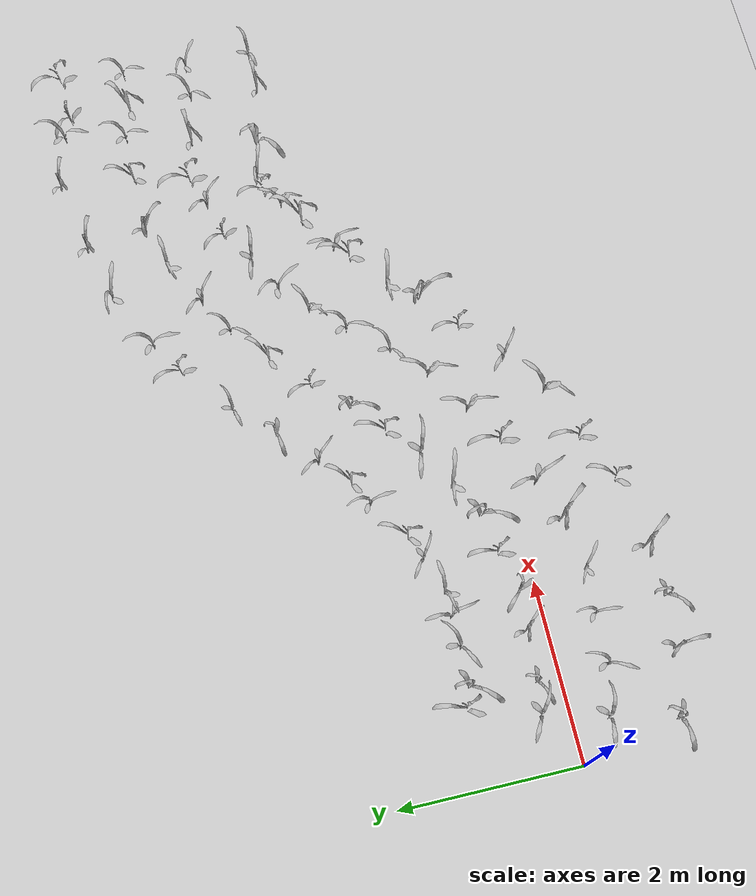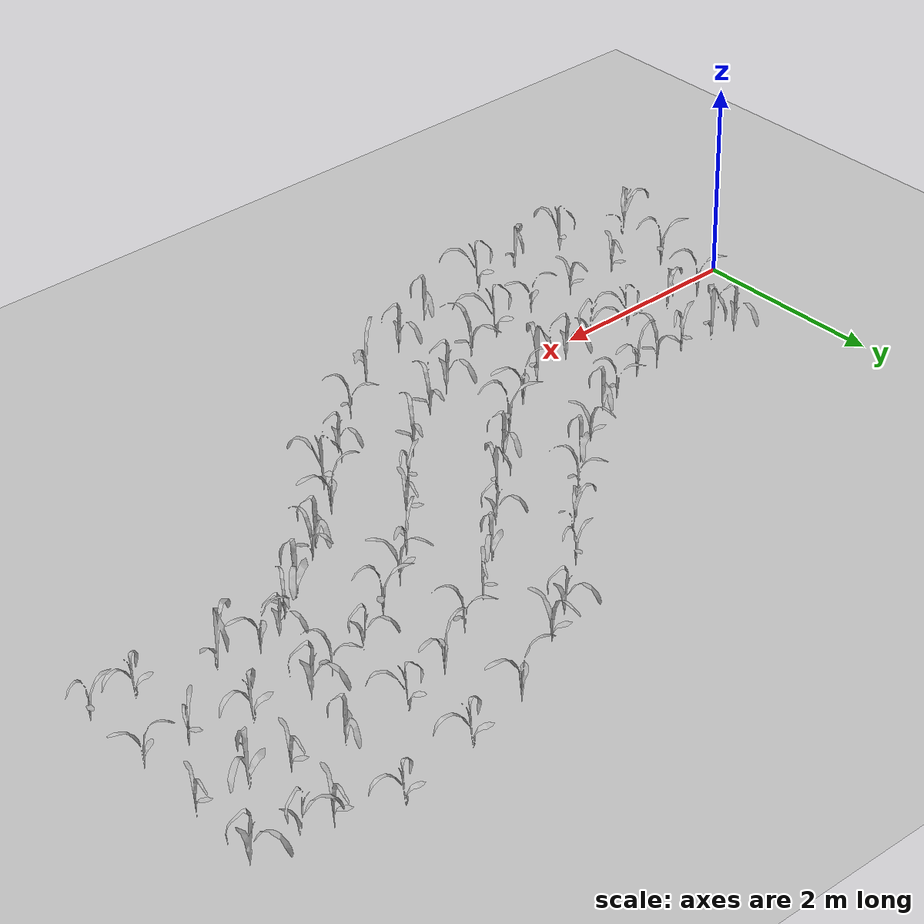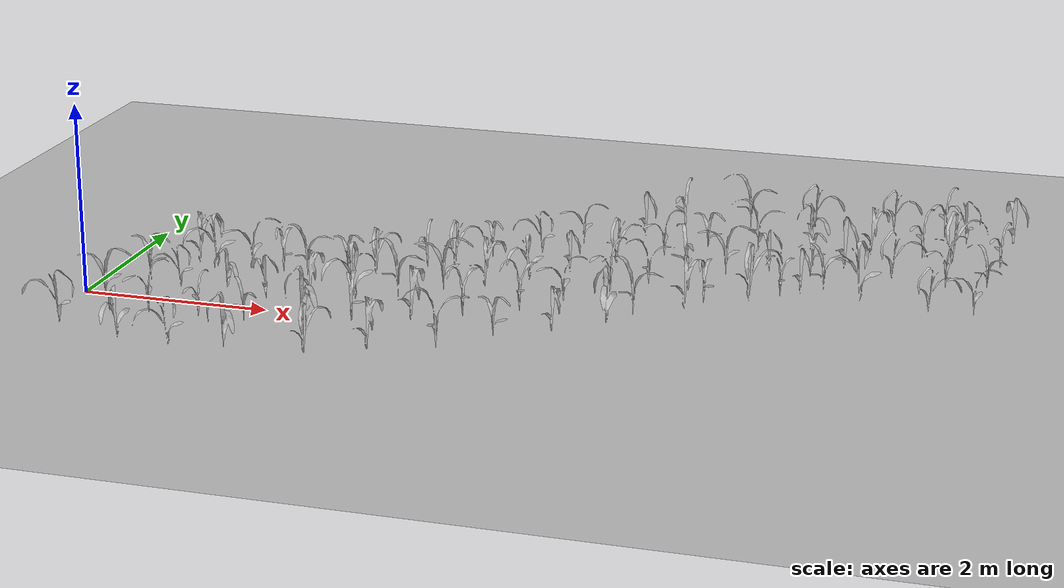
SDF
<sdf version="1.6">
 <world name="default">
  <light name="sun" type="directional">
   <pose>0 0 10 0 -0 0</pose>
   <diffuse>0.8 0.8 0.8 1</diffuse>
   <specular>0.2 0.2 0.2 1</specular>
   <attenuation>
    <range>1000</range>
    <constant>0.9</constant>
    <linear>0.01</linear>
    <quadratic>0.001</quadratic>
   </attenuation>
   <direction>-0.5 0.1 -0.9</direction>
  </light>
  <model name="ground_plane">
   <static>1</static>
   <link name="link">
    <collision name="collision">
     <geometry><plane><normal>0 0 1</normal><size>100 100</size></plane></geometry>
     <surface>
      <contact><collide_bitmask>65535</collide_bitmask></contact>
      <friction><ode><mu>100</mu><mu2>50</mu2></ode></friction>
     </surface>
    </collision>
    <visual name="visual">
     <cast_shadows>0</cast_shadows>
     <geometry><plane><normal>0 0 1</normal><size>100 100</size></plane></geometry>
     <material>
      <script><uri>file://media/materials/scripts/gazebo.material</uri><name>Gazebo/Grey</name></script>
     </material>
    </visual>
   </link>
  </model>
  <gravity>0 0 -9.8</gravity>
  <magnetic_field>6e-06 2.3e-05 -4.2e-05</magnetic_field>
  <atmosphere type="adiabatic"/>
  <physics name="default_physics" default="0" type="ode">
   <max_step_size>0.001</max_step_size>
   <real_time_factor>1</real_time_factor>
   <real_time_update_rate>1000</real_time_update_rate>
  </physics>
  <scene><ambient>0.4 0.4 0.4 1</ambient><background>0.7 0.7 0.7 1</background><shadows>1</shadows></scene>
  <audio><device>default</device></audio>
  <spherical_coordinates>
   <surface_model>EARTH_WGS84</surface_model>
   <latitude_deg>0</latitude_deg>
   <longitude_deg>0</longitude_deg>
   <elevation>0</elevation>
   <heading_deg>0</heading_deg>
  </spherical_coordinates>
  <model name="maize_02_0000">
   <pose>0.5852653367917549 0.3318975245804875 0.05 0 -0 4.819137196691981</pose>
   <link name="maize_02_0000_link">
    <inertial>
     <mass>5.0</mass>
     <inertia>
      <ixx>0.0033416667</ixx>
      <ixy>0</ixy>
      <ixz>0</ixz>
      <iyy>0.0033416667</iyy>
      <iyz>0</iyz>
      <izz>0.000016666667</izz>
     </inertia>
     <pose>0 0 0.1 0 0 0</pose>
    </inertial>
    <collision name="collision">
     <pose>0 0 0.2 0 -0 0</pose>
     <geometry><box><size>0.02 0.02 0.4</size></box></geometry>
     <surface><friction><ode><mu>10</mu><mu2>10</mu2></ode></friction></surface>
    </collision>
    <visual name="visual">
     <geometry>
      <mesh>
       <uri>model://maize_02/meshes/maize_02.dae</uri>
       <scale>0.6198655844902619 0.6198655844902619 0.6198655844902619</scale>
      </mesh>
     </geometry>
    </visual>
   </link>
  </model>
  <model name="maize_01_0001">
   <pose>0.819224740678983 1.0473308832072175 0.05 0 -0 2.1558350622808797</pose>
   <link name="maize_01_0001_link">
    <inertial>
     <mass>5.0</mass>
     <inertia>
      <ixx>0.0033416667</ixx>
      <ixy>0</ixy>
      <ixz>0</ixz>
      <iyy>0.0033416667</iyy>
      <iyz>0</iyz>
      <izz>0.000016666667</izz>
     </inertia>
     <pose>0 0 0.1 0 0 0</pose>
    </inertial>
    <collision name="collision">
     <pose>0 0 0.2 0 -0 0</pose>
     <geometry><box><size>0.02 0.02 0.4</size></box></geometry>
     <surface><friction><ode><mu>10</mu><mu2>10</mu2></ode></friction></surface>
    </collision>
    <visual name="visual">
     <geometry>
      <mesh>
       <uri>model://maize_01/meshes/maize_01.dae</uri>
       <scale>0.6231910097683236 0.6231910097683236 0.6231910097683236</scale>
      </mesh>
     </geometry>
    </visual>
   </link>
  </model>
  <model name="maize_02_0002">
   <pose>0.40558978321978284 -0.34852179317750154 0.05 0 -0 5.124807641884314</pose>
   <link name="maize_02_0002_link">
    <inertial>
     <mass>5.0</mass>
     <inertia>
      <ixx>0.0033416667</ixx>
      <ixy>0</ixy>
      <ixz>0</ixz>
      <iyy>0.0033416667</iyy>
      <iyz>0</iyz>
      <izz>0.000016666667</izz>
     </inertia>
     <pose>0 0 0.1 0 0 0</pose>
    </inertial>
    <collision name="collision">
     <pose>0 0 0.2 0 -0 0</pose>
     <geometry><box><size>0.02 0.02 0.4</size></box></geometry>
     <surface><friction><ode><mu>10</mu><mu2>10</mu2></ode></friction></surface>
    </collision>
    <visual name="visual">
     <geometry>
      <mesh>
       <uri>model://maize_02/meshes/maize_02.dae</uri>
       <scale>0.6528116234078092 0.6528116234078092 0.6528116234078092</scale>
      </mesh>
     </geometry>
    </visual>
   </link>
  </model>
  <model name="maize_01_0003">
   <pose>0.24168280885078264 -1.0580865629336622 0.05 0 -0 3.9816687229967505</pose>
   <link name="maize_01_0003_link">
    <inertial>
     <mass>5.0</mass>
     <inertia>
      <ixx>0.0033416667</ixx>
      <ixy>0</ixy>
      <ixz>0</ixz>
      <iyy>0.0033416667</iyy>
      <iyz>0</iyz>
      <izz>0.000016666667</izz>
     </inertia>
     <pose>0 0 0.1 0 0 0</pose>
    </inertial>
    <collision name="collision">
     <pose>0 0 0.2 0 -0 0</pose>
     <geometry><box><size>0.02 0.02 0.4</size></box></geometry>
     <surface><friction><ode><mu>10</mu><mu2>10</mu2></ode></friction></surface>
    </collision>
    <visual name="visual">
     <geometry>
      <mesh>
       <uri>model://maize_01/meshes/maize_01.dae</uri>
       <scale>0.6133527399428998 0.6133527399428998 0.6133527399428998</scale>
      </mesh>
     </geometry>
    </visual>
   </link>
  </model>
  <model name="maize_01_0004">
   <pose>0.9390161218849827 0.2778658560384204 0.05 0 -0 4.271016923427325</pose>
   <link name="maize_01_0004_link">
    <inertial>
     <mass>5.0</mass>
     <inertia>
      <ixx>0.0033416667</ixx>
      <ixy>0</ixy>
      <ixz>0</ixz>
      <iyy>0.0033416667</iyy>
      <iyz>0</iyz>
      <izz>0.000016666667</izz>
     </inertia>
     <pose>0 0 0.1 0 0 0</pose>
    </inertial>
    <collision name="collision">
     <pose>0 0 0.2 0 -0 0</pose>
     <geometry><box><size>0.02 0.02 0.4</size></box></geometry>
     <surface><friction><ode><mu>10</mu><mu2>10</mu2></ode></friction></surface>
    </collision>
    <visual name="visual">
     <geometry>
      <mesh>
       <uri>model://maize_01/meshes/maize_01.dae</uri>
       <scale>0.5013892831783784 0.5013892831783784 0.5013892831783784</scale>
      </mesh>
     </geometry>
    </visual>
   </link>
  </model>
  <model name="maize_01_0005">
   <pose>1.0433240931990193 0.9779338062818309 0.05 0 -0 4.773157440183226</pose>
   <link name="maize_01_0005_link">
    <inertial>
     <mass>5.0</mass>
     <inertia>
      <ixx>0.0033416667</ixx>
      <ixy>0</ixy>
      <ixz>0</ixz>
      <iyy>0.0033416667</iyy>
      <iyz>0</iyz>
      <izz>0.000016666667</izz>
     </inertia>
     <pose>0 0 0.1 0 0 0</pose>
    </inertial>
    <collision name="collision">
     <pose>0 0 0.2 0 -0 0</pose>
     <geometry><box><size>0.02 0.02 0.4</size></box></geometry>
     <surface><friction><ode><mu>10</mu><mu2>10</mu2></ode></friction></surface>
    </collision>
    <visual name="visual">
     <geometry>
      <mesh>
       <uri>model://maize_01/meshes/maize_01.dae</uri>
       <scale>0.6386361690071659 0.6386361690071659 0.6386361690071659</scale>
      </mesh>
     </geometry>
    </visual>
   </link>
  </model>
  <model name="maize_02_0006">
   <pose>0.9435436977935228 -0.5009072258348778 0.05 0 -0 0.07977521289463807</pose>
   <link name="maize_02_0006_link">
    <inertial>
     <mass>5.0</mass>
     <inertia>
      <ixx>0.0033416667</ixx>
      <ixy>0</ixy>
      <ixz>0</ixz>
      <iyy>0.0033416667</iyy>
      <iyz>0</iyz>
      <izz>0.000016666667</izz>
     </inertia>
     <pose>0 0 0.1 0 0 0</pose>
    </inertial>
    <collision name="collision">
     <pose>0 0 0.2 0 -0 0</pose>
     <geometry><box><size>0.02 0.02 0.4</size></box></geometry>
     <surface><friction><ode><mu>10</mu><mu2>10</mu2></ode></friction></surface>
    </collision>
    <visual name="visual">
     <geometry>
      <mesh>
       <uri>model://maize_02/meshes/maize_02.dae</uri>
       <scale>0.5684113326045124 0.5684113326045124 0.5684113326045124</scale>
      </mesh>
     </geometry>
    </visual>
   </link>
  </model>
  <model name="maize_01_0007">
   <pose>0.9520983835941816 -1.2447676150098879 0.05 0 -0 5.541592673597331</pose>
   <link name="maize_01_0007_link">
    <inertial>
     <mass>5.0</mass>
     <inertia>
      <ixx>0.0033416667</ixx>
      <ixy>0</ixy>
      <ixz>0</ixz>
      <iyy>0.0033416667</iyy>
      <iyz>0</iyz>
      <izz>0.000016666667</izz>
     </inertia>
     <pose>0 0 0.1 0 0 0</pose>
    </inertial>
    <collision name="collision">
     <pose>0 0 0.2 0 -0 0</pose>
     <geometry><box><size>0.02 0.02 0.4</size></box></geometry>
     <surface><friction><ode><mu>10</mu><mu2>10</mu2></ode></friction></surface>
    </collision>
    <visual name="visual">
     <geometry>
      <mesh>
       <uri>model://maize_01/meshes/maize_01.dae</uri>
       <scale>0.5812379114549232 0.5812379114549232 0.5812379114549232</scale>
      </mesh>
     </geometry>
    </visual>
   </link>
  </model>
  <model name="maize_01_0008">
   <pose>1.4710803604021425 0.251955824354667 0.05 0 -0 6.238931316800727</pose>
   <link name="maize_01_0008_link">
    <inertial>
     <mass>5.0</mass>
     <inertia>
      <ixx>0.0033416667</ixx>
      <ixy>0</ixy>
      <ixz>0</ixz>
      <iyy>0.0033416667</iyy>
      <iyz>0</iyz>
      <izz>0.000016666667</izz>
     </inertia>
     <pose>0 0 0.1 0 0 0</pose>
    </inertial>
    <collision name="collision">
     <pose>0 0 0.2 0 -0 0</pose>
     <geometry><box><size>0.02 0.02 0.4</size></box></geometry>
     <surface><friction><ode><mu>10</mu><mu2>10</mu2></ode></friction></surface>
    </collision>
    <visual name="visual">
     <geometry>
      <mesh>
       <uri>model://maize_01/meshes/maize_01.dae</uri>
       <scale>0.5223644311173579 0.5223644311173579 0.5223644311173579</scale>
      </mesh>
     </geometry>
    </visual>
   </link>
  </model>
  <model name="maize_02_0009">
   <pose>1.4540257556802145 0.9679712613130649 0.05 0 -0 5.768217206137263</pose>
   <link name="maize_02_0009_link">
    <inertial>
     <mass>5.0</mass>
     <inertia>
      <ixx>0.0033416667</ixx>
      <ixy>0</ixy>
      <ixz>0</ixz>
      <iyy>0.0033416667</iyy>
      <iyz>0</iyz>
      <izz>0.000016666667</izz>
     </inertia>
     <pose>0 0 0.1 0 0 0</pose>
    </inertial>
    <collision name="collision">
     <pose>0 0 0.2 0 -0 0</pose>
     <geometry><box><size>0.02 0.02 0.4</size></box></geometry>
     <surface><friction><ode><mu>10</mu><mu2>10</mu2></ode></friction></surface>
    </collision>
    <visual name="visual">
     <geometry>
      <mesh>
       <uri>model://maize_02/meshes/maize_02.dae</uri>
       <scale>0.6155631847034542 0.6155631847034542 0.6155631847034542</scale>
      </mesh>
     </geometry>
    </visual>
   </link>
  </model>
  <model name="maize_02_0010">
   <pose>1.4918015879454176 -0.5199005328881918 0.05 0 -0 0.46721395192465426</pose>
   <link name="maize_02_0010_link">
    <inertial>
     <mass>5.0</mass>
     <inertia>
      <ixx>0.0033416667</ixx>
      <ixy>0</ixy>
      <ixz>0</ixz>
      <iyy>0.0033416667</iyy>
      <iyz>0</iyz>
      <izz>0.000016666667</izz>
     </inertia>
     <pose>0 0 0.1 0 0 0</pose>
    </inertial>
    <collision name="collision">
     <pose>0 0 0.2 0 -0 0</pose>
     <geometry><box><size>0.02 0.02 0.4</size></box></geometry>
     <surface><friction><ode><mu>10</mu><mu2>10</mu2></ode></friction></surface>
    </collision>
    <visual name="visual">
     <geometry>
      <mesh>
       <uri>model://maize_02/meshes/maize_02.dae</uri>
       <scale>0.5000797023428499 0.5000797023428499 0.5000797023428499</scale>
      </mesh>
     </geometry>
    </visual>
   </link>
  </model>
  <model name="maize_01_0011">
   <pose>1.515319801560635 -1.2987714635864087 0.05 0 -0 4.596360872219469</pose>
   <link name="maize_01_0011_link">
    <inertial>
     <mass>5.0</mass>
     <inertia>
      <ixx>0.0033416667</ixx>
      <ixy>0</ixy>
      <ixz>0</ixz>
      <iyy>0.0033416667</iyy>
      <iyz>0</iyz>
      <izz>0.000016666667</izz>
     </inertia>
     <pose>0 0 0.1 0 0 0</pose>
    </inertial>
    <collision name="collision">
     <pose>0 0 0.2 0 -0 0</pose>
     <geometry><box><size>0.02 0.02 0.4</size></box></geometry>
     <surface><friction><ode><mu>10</mu><mu2>10</mu2></ode></friction></surface>
    </collision>
    <visual name="visual">
     <geometry>
      <mesh>
       <uri>model://maize_01/meshes/maize_01.dae</uri>
       <scale>0.5441755178383955 0.5441755178383955 0.5441755178383955</scale>
      </mesh>
     </geometry>
    </visual>
   </link>
  </model>
  <model name="maize_01_0012">
   <pose>1.9238771021630594 0.1877942131749205 0.05 0 -0 3.1945023329080233</pose>
   <link name="maize_01_0012_link">
    <inertial>
     <mass>5.0</mass>
     <inertia>
      <ixx>0.0033416667</ixx>
      <ixy>0</ixy>
      <ixz>0</ixz>
      <iyy>0.0033416667</iyy>
      <iyz>0</iyz>
      <izz>0.000016666667</izz>
     </inertia>
     <pose>0 0 0.1 0 0 0</pose>
    </inertial>
    <collision name="collision">
     <pose>0 0 0.2 0 -0 0</pose>
     <geometry><box><size>0.02 0.02 0.4</size></box></geometry>
     <surface><friction><ode><mu>10</mu><mu2>10</mu2></ode></friction></surface>
    </collision>
    <visual name="visual">
     <geometry>
      <mesh>
       <uri>model://maize_01/meshes/maize_01.dae</uri>
       <scale>0.5189079695927395 0.5189079695927395 0.5189079695927395</scale>
      </mesh>
     </geometry>
    </visual>
   </link>
  </model>
  <model name="maize_02_0013">
   <pose>1.796037262723127 0.9823309842579532 0.05 0 -0 3.8167087248394163</pose>
   <link name="maize_02_0013_link">
    <inertial>
     <mass>5.0</mass>
     <inertia>
      <ixx>0.0033416667</ixx>
      <ixy>0</ixy>
      <ixz>0</ixz>
      <iyy>0.0033416667</iyy>
      <iyz>0</iyz>
      <izz>0.000016666667</izz>
     </inertia>
     <pose>0 0 0.1 0 0 0</pose>
    </inertial>
    <collision name="collision">
     <pose>0 0 0.2 0 -0 0</pose>
     <geometry><box><size>0.02 0.02 0.4</size></box></geometry>
     <surface><friction><ode><mu>10</mu><mu2>10</mu2></ode></friction></surface>
    </collision>
    <visual name="visual">
     <geometry>
      <mesh>
       <uri>model://maize_02/meshes/maize_02.dae</uri>
       <scale>0.5849789956032055 0.5849789956032055 0.5849789956032055</scale>
      </mesh>
     </geometry>
    </visual>
   </link>
  </model>
  <model name="maize_02_0014">
   <pose>1.9917397850975298 -0.5538407257475357 0.05 0 -0 1.556746249958554</pose>
   <link name="maize_02_0014_link">
    <inertial>
     <mass>5.0</mass>
     <inertia>
      <ixx>0.0033416667</ixx>
      <ixy>0</ixy>
      <ixz>0</ixz>
      <iyy>0.0033416667</iyy>
      <iyz>0</iyz>
      <izz>0.000016666667</izz>
     </inertia>
     <pose>0 0 0.1 0 0 0</pose>
    </inertial>
    <collision name="collision">
     <pose>0 0 0.2 0 -0 0</pose>
     <geometry><box><size>0.02 0.02 0.4</size></box></geometry>
     <surface><friction><ode><mu>10</mu><mu2>10</mu2></ode></friction></surface>
    </collision>
    <visual name="visual">
     <geometry>
      <mesh>
       <uri>model://maize_02/meshes/maize_02.dae</uri>
       <scale>0.5020388727855789 0.5020388727855789 0.5020388727855789</scale>
      </mesh>
     </geometry>
    </visual>
   </link>
  </model>
  <model name="maize_01_0015">
   <pose>2.0702681742821123 -1.236859452738148 0.05 0 -0 6.171946836271607</pose>
   <link name="maize_01_0015_link">
    <inertial>
     <mass>5.0</mass>
     <inertia>
      <ixx>0.0033416667</ixx>
      <ixy>0</ixy>
      <ixz>0</ixz>
      <iyy>0.0033416667</iyy>
      <iyz>0</iyz>
      <izz>0.000016666667</izz>
     </inertia>
     <pose>0 0 0.1 0 0 0</pose>
    </inertial>
    <collision name="collision">
     <pose>0 0 0.2 0 -0 0</pose>
     <geometry><box><size>0.02 0.02 0.4</size></box></geometry>
     <surface><friction><ode><mu>10</mu><mu2>10</mu2></ode></friction></surface>
    </collision>
    <visual name="visual">
     <geometry>
      <mesh>
       <uri>model://maize_01/meshes/maize_01.dae</uri>
       <scale>0.6263677373690738 0.6263677373690738 0.6263677373690738</scale>
      </mesh>
     </geometry>
    </visual>
   </link>
  </model>
  <model name="maize_01_0016">
   <pose>2.3523107436248694 0.314003701111601 0.05 0 -0 2.3253177278490385</pose>
   <link name="maize_01_0016_link">
    <inertial>
     <mass>5.0</mass>
     <inertia>
      <ixx>0.0033416667</ixx>
      <ixy>0</ixy>
      <ixz>0</ixz>
      <iyy>0.0033416667</iyy>
      <iyz>0</iyz>
      <izz>0.000016666667</izz>
     </inertia>
     <pose>0 0 0.1 0 0 0</pose>
    </inertial>
    <collision name="collision">
     <pose>0 0 0.2 0 -0 0</pose>
     <geometry><box><size>0.02 0.02 0.4</size></box></geometry>
     <surface><friction><ode><mu>10</mu><mu2>10</mu2></ode></friction></surface>
    </collision>
    <visual name="visual">
     <geometry>
      <mesh>
       <uri>model://maize_01/meshes/maize_01.dae</uri>
       <scale>0.5847231730509037 0.5847231730509037 0.5847231730509037</scale>
      </mesh>
     </geometry>
    </visual>
   </link>
  </model>
  <model name="maize_02_0017">
   <pose>2.0594638042464877 0.9808779157767082 0.05 0 -0 2.268823572105541</pose>
   <link name="maize_02_0017_link">
    <inertial>
     <mass>5.0</mass>
     <inertia>
      <ixx>0.0033416667</ixx>
      <ixy>0</ixy>
      <ixz>0</ixz>
      <iyy>0.0033416667</iyy>
      <iyz>0</iyz>
      <izz>0.000016666667</izz>
     </inertia>
     <pose>0 0 0.1 0 0 0</pose>
    </inertial>
    <collision name="collision">
     <pose>0 0 0.2 0 -0 0</pose>
     <geometry><box><size>0.02 0.02 0.4</size></box></geometry>
     <surface><friction><ode><mu>10</mu><mu2>10</mu2></ode></friction></surface>
    </collision>
    <visual name="visual">
     <geometry>
      <mesh>
       <uri>model://maize_02/meshes/maize_02.dae</uri>
       <scale>0.5988593081619046 0.5988593081619046 0.5988593081619046</scale>
      </mesh>
     </geometry>
    </visual>
   </link>
  </model>
  <model name="maize_01_0018">
   <pose>2.563373309769741 -0.43797303256134 0.05 0 -0 6.221016702236848</pose>
   <link name="maize_01_0018_link">
    <inertial>
     <mass>5.0</mass>
     <inertia>
      <ixx>0.0033416667</ixx>
      <ixy>0</ixy>
      <ixz>0</ixz>
      <iyy>0.0033416667</iyy>
      <iyz>0</iyz>
      <izz>0.000016666667</izz>
     </inertia>
     <pose>0 0 0.1 0 0 0</pose>
    </inertial>
    <collision name="collision">
     <pose>0 0 0.2 0 -0 0</pose>
     <geometry><box><size>0.02 0.02 0.4</size></box></geometry>
     <surface><friction><ode><mu>10</mu><mu2>10</mu2></ode></friction></surface>
    </collision>
    <visual name="visual">
     <geometry>
      <mesh>
       <uri>model://maize_01/meshes/maize_01.dae</uri>
       <scale>0.674993146854803 0.674993146854803 0.674993146854803</scale>
      </mesh>
     </geometry>
    </visual>
   </link>
  </model>
  <model name="maize_01_0019">
   <pose>2.861835509038293 -1.141784677089345 0.05 0 -0 1.873990965419019</pose>
   <link name="maize_01_0019_link">
    <inertial>
     <mass>5.0</mass>
     <inertia>
      <ixx>0.0033416667</ixx>
      <ixy>0</ixy>
      <ixz>0</ixz>
      <iyy>0.0033416667</iyy>
      <iyz>0</iyz>
      <izz>0.000016666667</izz>
     </inertia>
     <pose>0 0 0.1 0 0 0</pose>
    </inertial>
    <collision name="collision">
     <pose>0 0 0.2 0 -0 0</pose>
     <geometry><box><size>0.02 0.02 0.4</size></box></geometry>
     <surface><friction><ode><mu>10</mu><mu2>10</mu2></ode></friction></surface>
    </collision>
    <visual name="visual">
     <geometry>
      <mesh>
       <uri>model://maize_01/meshes/maize_01.dae</uri>
       <scale>0.5777262842857496 0.5777262842857496 0.5777262842857496</scale>
      </mesh>
     </geometry>
    </visual>
   </link>
  </model>
  <model name="maize_01_0020">
   <pose>2.7974986973740203 0.3984434908552974 0.05 0 -0 4.967490776944291</pose>
   <link name="maize_01_0020_link">
    <inertial>
     <mass>5.0</mass>
     <inertia>
      <ixx>0.0033416667</ixx>
      <ixy>0</ixy>
      <ixz>0</ixz>
      <iyy>0.0033416667</iyy>
      <iyz>0</iyz>
      <izz>0.000016666667</izz>
     </inertia>
     <pose>0 0 0.1 0 0 0</pose>
    </inertial>
    <collision name="collision">
     <pose>0 0 0.2 0 -0 0</pose>
     <geometry><box><size>0.02 0.02 0.4</size></box></geometry>
     <surface><friction><ode><mu>10</mu><mu2>10</mu2></ode></friction></surface>
    </collision>
    <visual name="visual">
     <geometry>
      <mesh>
       <uri>model://maize_01/meshes/maize_01.dae</uri>
       <scale>0.6812627631122814 0.6812627631122814 0.6812627631122814</scale>
      </mesh>
     </geometry>
    </visual>
   </link>
  </model>
  <model name="maize_02_0021">
   <pose>2.460382011911631 1.121799512558572 0.05 0 -0 4.7214015216645375</pose>
   <link name="maize_02_0021_link">
    <inertial>
     <mass>5.0</mass>
     <inertia>
      <ixx>0.0033416667</ixx>
      <ixy>0</ixy>
      <ixz>0</ixz>
      <iyy>0.0033416667</iyy>
      <iyz>0</iyz>
      <izz>0.000016666667</izz>
     </inertia>
     <pose>0 0 0.1 0 0 0</pose>
    </inertial>
    <collision name="collision">
     <pose>0 0 0.2 0 -0 0</pose>
     <geometry><box><size>0.02 0.02 0.4</size></box></geometry>
     <surface><friction><ode><mu>10</mu><mu2>10</mu2></ode></friction></surface>
    </collision>
    <visual name="visual">
     <geometry>
      <mesh>
       <uri>model://maize_02/meshes/maize_02.dae</uri>
       <scale>0.5156354718797089 0.5156354718797089 0.5156354718797089</scale>
      </mesh>
     </geometry>
    </visual>
   </link>
  </model>
  <model name="maize_02_0022">
   <pose>3.0237332085631774 -0.27581309665760934 0.05 0 -0 4.012740057833342</pose>
   <link name="maize_02_0022_link">
    <inertial>
     <mass>5.0</mass>
     <inertia>
      <ixx>0.0033416667</ixx>
      <ixy>0</ixy>
      <ixz>0</ixz>
      <iyy>0.0033416667</iyy>
      <iyz>0</iyz>
      <izz>0.000016666667</izz>
     </inertia>
     <pose>0 0 0.1 0 0 0</pose>
    </inertial>
    <collision name="collision">
     <pose>0 0 0.2 0 -0 0</pose>
     <geometry><box><size>0.02 0.02 0.4</size></box></geometry>
     <surface><friction><ode><mu>10</mu><mu2>10</mu2></ode></friction></surface>
    </collision>
    <visual name="visual">
     <geometry>
      <mesh>
       <uri>model://maize_02/meshes/maize_02.dae</uri>
       <scale>0.657859032380797 0.657859032380797 0.657859032380797</scale>
      </mesh>
     </geometry>
    </visual>
   </link>
  </model>
  <model name="maize_01_0023">
   <pose>3.4111367063759492 -0.8863992666368435 0.05 0 -0 2.2832807923442737</pose>
   <link name="maize_01_0023_link">
    <inertial>
     <mass>5.0</mass>
     <inertia>
      <ixx>0.0033416667</ixx>
      <ixy>0</ixy>
      <ixz>0</ixz>
      <iyy>0.0033416667</iyy>
      <iyz>0</iyz>
      <izz>0.000016666667</izz>
     </inertia>
     <pose>0 0 0.1 0 0 0</pose>
    </inertial>
    <collision name="collision">
     <pose>0 0 0.2 0 -0 0</pose>
     <geometry><box><size>0.02 0.02 0.4</size></box></geometry>
     <surface><friction><ode><mu>10</mu><mu2>10</mu2></ode></friction></surface>
    </collision>
    <visual name="visual">
     <geometry>
      <mesh>
       <uri>model://maize_01/meshes/maize_01.dae</uri>
       <scale>0.599202152196202 0.599202152196202 0.599202152196202</scale>
      </mesh>
     </geometry>
    </visual>
   </link>
  </model>
  <model name="maize_02_0024">
   <pose>3.187744665740914 0.6193244460786459 0.05 0 -0 1.915602899776297</pose>
   <link name="maize_02_0024_link">
    <inertial>
     <mass>5.0</mass>
     <inertia>
      <ixx>0.0033416667</ixx>
      <ixy>0</ixy>
      <ixz>0</ixz>
      <iyy>0.0033416667</iyy>
      <iyz>0</iyz>
      <izz>0.000016666667</izz>
     </inertia>
     <pose>0 0 0.1 0 0 0</pose>
    </inertial>
    <collision name="collision">
     <pose>0 0 0.2 0 -0 0</pose>
     <geometry><box><size>0.02 0.02 0.4</size></box></geometry>
     <surface><friction><ode><mu>10</mu><mu2>10</mu2></ode></friction></surface>
    </collision>
    <visual name="visual">
     <geometry>
      <mesh>
       <uri>model://maize_02/meshes/maize_02.dae</uri>
       <scale>0.6491385240156974 0.6491385240156974 0.6491385240156974</scale>
      </mesh>
     </geometry>
    </visual>
   </link>
  </model>
  <model name="maize_01_0025">
   <pose>2.7381442768128883 1.2120958748460364 0.05 0 -0 1.823986729176547</pose>
   <link name="maize_01_0025_link">
    <inertial>
     <mass>5.0</mass>
     <inertia>
      <ixx>0.0033416667</ixx>
      <ixy>0</ixy>
      <ixz>0</ixz>
      <iyy>0.0033416667</iyy>
      <iyz>0</iyz>
      <izz>0.000016666667</izz>
     </inertia>
     <pose>0 0 0.1 0 0 0</pose>
    </inertial>
    <collision name="collision">
     <pose>0 0 0.2 0 -0 0</pose>
     <geometry><box><size>0.02 0.02 0.4</size></box></geometry>
     <surface><friction><ode><mu>10</mu><mu2>10</mu2></ode></friction></surface>
    </collision>
    <visual name="visual">
     <geometry>
      <mesh>
       <uri>model://maize_01/meshes/maize_01.dae</uri>
       <scale>0.5687859275631976 0.5687859275631976 0.5687859275631976</scale>
      </mesh>
     </geometry>
    </visual>
   </link>
  </model>
  <model name="maize_01_0026">
   <pose>3.5622430096199165 -0.030292088759010113 0.05 0 -0 2.3895884762900703</pose>
   <link name="maize_01_0026_link">
    <inertial>
     <mass>5.0</mass>
     <inertia>
      <ixx>0.0033416667</ixx>
      <ixy>0</ixy>
      <ixz>0</ixz>
      <iyy>0.0033416667</iyy>
      <iyz>0</iyz>
      <izz>0.000016666667</izz>
     </inertia>
     <pose>0 0 0.1 0 0 0</pose>
    </inertial>
    <collision name="collision">
     <pose>0 0 0.2 0 -0 0</pose>
     <geometry><box><size>0.02 0.02 0.4</size></box></geometry>
     <surface><friction><ode><mu>10</mu><mu2>10</mu2></ode></friction></surface>
    </collision>
    <visual name="visual">
     <geometry>
      <mesh>
       <uri>model://maize_01/meshes/maize_01.dae</uri>
       <scale>0.651003261346263 0.651003261346263 0.651003261346263</scale>
      </mesh>
     </geometry>
    </visual>
   </link>
  </model>
  <model name="maize_02_0027">
   <pose>4.024046199321598 -0.6432361299946997 0.05 0 -0 2.7971562792821607</pose>
   <link name="maize_02_0027_link">
    <inertial>
     <mass>5.0</mass>
     <inertia>
      <ixx>0.0033416667</ixx>
      <ixy>0</ixy>
      <ixz>0</ixz>
      <iyy>0.0033416667</iyy>
      <iyz>0</iyz>
      <izz>0.000016666667</izz>
     </inertia>
     <pose>0 0 0.1 0 0 0</pose>
    </inertial>
    <collision name="collision">
     <pose>0 0 0.2 0 -0 0</pose>
     <geometry><box><size>0.02 0.02 0.4</size></box></geometry>
     <surface><friction><ode><mu>10</mu><mu2>10</mu2></ode></friction></surface>
    </collision>
    <visual name="visual">
     <geometry>
      <mesh>
       <uri>model://maize_02/meshes/maize_02.dae</uri>
       <scale>0.6805788621275966 0.6805788621275966 0.6805788621275966</scale>
      </mesh>
     </geometry>
    </visual>
   </link>
  </model>
  <model name="maize_02_0028">
   <pose>3.592722145805524 0.8710600447686613 0.05 0 -0 5.066617296605854</pose>
   <link name="maize_02_0028_link">
    <inertial>
     <mass>5.0</mass>
     <inertia>
      <ixx>0.0033416667</ixx>
      <ixy>0</ixy>
      <ixz>0</ixz>
      <iyy>0.0033416667</iyy>
      <iyz>0</iyz>
      <izz>0.000016666667</izz>
     </inertia>
     <pose>0 0 0.1 0 0 0</pose>
    </inertial>
    <collision name="collision">
     <pose>0 0 0.2 0 -0 0</pose>
     <geometry><box><size>0.02 0.02 0.4</size></box></geometry>
     <surface><friction><ode><mu>10</mu><mu2>10</mu2></ode></friction></surface>
    </collision>
    <visual name="visual">
     <geometry>
      <mesh>
       <uri>model://maize_02/meshes/maize_02.dae</uri>
       <scale>0.6786293050277437 0.6786293050277437 0.6786293050277437</scale>
      </mesh>
     </geometry>
    </visual>
   </link>
  </model>
  <model name="maize_02_0029">
   <pose>3.1907145028444757 1.527890867731571 0.05 0 -0 0.6625776207973766</pose>
   <link name="maize_02_0029_link">
    <inertial>
     <mass>5.0</mass>
     <inertia>
      <ixx>0.0033416667</ixx>
      <ixy>0</ixy>
      <ixz>0</ixz>
      <iyy>0.0033416667</iyy>
      <iyz>0</iyz>
      <izz>0.000016666667</izz>
     </inertia>
     <pose>0 0 0.1 0 0 0</pose>
    </inertial>
    <collision name="collision">
     <pose>0 0 0.2 0 -0 0</pose>
     <geometry><box><size>0.02 0.02 0.4</size></box></geometry>
     <surface><friction><ode><mu>10</mu><mu2>10</mu2></ode></friction></surface>
    </collision>
    <visual name="visual">
     <geometry>
      <mesh>
       <uri>model://maize_02/meshes/maize_02.dae</uri>
       <scale>0.5414249144522247 0.5414249144522247 0.5414249144522247</scale>
      </mesh>
     </geometry>
    </visual>
   </link>
  </model>
  <model name="maize_02_0030">
   <pose>4.0045292279793445 0.2382221796570852 0.05 0 -0 3.4805201987972127</pose>
   <link name="maize_02_0030_link">
    <inertial>
     <mass>5.0</mass>
     <inertia>
      <ixx>0.0033416667</ixx>
      <ixy>0</ixy>
      <ixz>0</ixz>
      <iyy>0.0033416667</iyy>
      <iyz>0</iyz>
      <izz>0.000016666667</izz>
     </inertia>
     <pose>0 0 0.1 0 0 0</pose>
    </inertial>
    <collision name="collision">
     <pose>0 0 0.2 0 -0 0</pose>
     <geometry><box><size>0.02 0.02 0.4</size></box></geometry>
     <surface><friction><ode><mu>10</mu><mu2>10</mu2></ode></friction></surface>
    </collision>
    <visual name="visual">
     <geometry>
      <mesh>
       <uri>model://maize_02/meshes/maize_02.dae</uri>
       <scale>0.6182009282914313 0.6182009282914313 0.6182009282914313</scale>
      </mesh>
     </geometry>
    </visual>
   </link>
  </model>
  <model name="maize_02_0031">
   <pose>4.4973108184964 -0.3032836574257594 0.05 0 -0 4.622835124000114</pose>
   <link name="maize_02_0031_link">
    <inertial>
     <mass>5.0</mass>
     <inertia>
      <ixx>0.0033416667</ixx>
      <ixy>0</ixy>
      <ixz>0</ixz>
      <iyy>0.0033416667</iyy>
      <iyz>0</iyz>
      <izz>0.000016666667</izz>
     </inertia>
     <pose>0 0 0.1 0 0 0</pose>
    </inertial>
    <collision name="collision">
     <pose>0 0 0.2 0 -0 0</pose>
     <geometry><box><size>0.02 0.02 0.4</size></box></geometry>
     <surface><friction><ode><mu>10</mu><mu2>10</mu2></ode></friction></surface>
    </collision>
    <visual name="visual">
     <geometry>
      <mesh>
       <uri>model://maize_02/meshes/maize_02.dae</uri>
       <scale>0.5380292373040949 0.5380292373040949 0.5380292373040949</scale>
      </mesh>
     </geometry>
    </visual>
   </link>
  </model>
  <model name="maize_01_0032">
   <pose>3.9420037278024034 1.170057710798335 0.05 0 -0 2.0346655031060488</pose>
   <link name="maize_01_0032_link">
    <inertial>
     <mass>5.0</mass>
     <inertia>
      <ixx>0.0033416667</ixx>
      <ixy>0</ixy>
      <ixz>0</ixz>
      <iyy>0.0033416667</iyy>
      <iyz>0</iyz>
      <izz>0.000016666667</izz>
     </inertia>
     <pose>0 0 0.1 0 0 0</pose>
    </inertial>
    <collision name="collision">
     <pose>0 0 0.2 0 -0 0</pose>
     <geometry><box><size>0.02 0.02 0.4</size></box></geometry>
     <surface><friction><ode><mu>10</mu><mu2>10</mu2></ode></friction></surface>
    </collision>
    <visual name="visual">
     <geometry>
      <mesh>
       <uri>model://maize_01/meshes/maize_01.dae</uri>
       <scale>0.5969374568946713 0.5969374568946713 0.5969374568946713</scale>
      </mesh>
     </geometry>
    </visual>
   </link>
  </model>
  <model name="maize_01_0033">
   <pose>3.454893269396232 1.6676647118103094 0.05 0 -0 1.6541569770463145</pose>
   <link name="maize_01_0033_link">
    <inertial>
     <mass>5.0</mass>
     <inertia>
      <ixx>0.0033416667</ixx>
      <ixy>0</ixy>
      <ixz>0</ixz>
      <iyy>0.0033416667</iyy>
      <iyz>0</iyz>
      <izz>0.000016666667</izz>
     </inertia>
     <pose>0 0 0.1 0 0 0</pose>
    </inertial>
    <collision name="collision">
     <pose>0 0 0.2 0 -0 0</pose>
     <geometry><box><size>0.02 0.02 0.4</size></box></geometry>
     <surface><friction><ode><mu>10</mu><mu2>10</mu2></ode></friction></surface>
    </collision>
    <visual name="visual">
     <geometry>
      <mesh>
       <uri>model://maize_01/meshes/maize_01.dae</uri>
       <scale>0.5715888245469294 0.5715888245469294 0.5715888245469294</scale>
      </mesh>
     </geometry>
    </visual>
   </link>
  </model>
  <model name="maize_02_0034">
   <pose>4.493978532254982 0.5687133431955295 0.05 0 -0 3.310158454012028</pose>
   <link name="maize_02_0034_link">
    <inertial>
     <mass>5.0</mass>
     <inertia>
      <ixx>0.0033416667</ixx>
      <ixy>0</ixy>
      <ixz>0</ixz>
      <iyy>0.0033416667</iyy>
      <iyz>0</iyz>
      <izz>0.000016666667</izz>
     </inertia>
     <pose>0 0 0.1 0 0 0</pose>
    </inertial>
    <collision name="collision">
     <pose>0 0 0.2 0 -0 0</pose>
     <geometry><box><size>0.02 0.02 0.4</size></box></geometry>
     <surface><friction><ode><mu>10</mu><mu2>10</mu2></ode></friction></surface>
    </collision>
    <visual name="visual">
     <geometry>
      <mesh>
       <uri>model://maize_02/meshes/maize_02.dae</uri>
       <scale>0.6318200602071443 0.6318200602071443 0.6318200602071443</scale>
      </mesh>
     </geometry>
    </visual>
   </link>
  </model>
  <model name="maize_01_0035">
   <pose>4.97444595073593 0.08621169543100017 0.05 0 -0 2.427624297971031</pose>
   <link name="maize_01_0035_link">
    <inertial>
     <mass>5.0</mass>
     <inertia>
      <ixx>0.0033416667</ixx>
      <ixy>0</ixy>
      <ixz>0</ixz>
      <iyy>0.0033416667</iyy>
      <iyz>0</iyz>
      <izz>0.000016666667</izz>
     </inertia>
     <pose>0 0 0.1 0 0 0</pose>
    </inertial>
    <collision name="collision">
     <pose>0 0 0.2 0 -0 0</pose>
     <geometry><box><size>0.02 0.02 0.4</size></box></geometry>
     <surface><friction><ode><mu>10</mu><mu2>10</mu2></ode></friction></surface>
    </collision>
    <visual name="visual">
     <geometry>
      <mesh>
       <uri>model://maize_01/meshes/maize_01.dae</uri>
       <scale>0.5274171438781382 0.5274171438781382 0.5274171438781382</scale>
      </mesh>
     </geometry>
    </visual>
   </link>
  </model>
  <model name="maize_01_0036">
   <pose>4.3148591834196885 1.4918823057127428 0.05 0 -0 5.05493490906569</pose>
   <link name="maize_01_0036_link">
    <inertial>
     <mass>5.0</mass>
     <inertia>
      <ixx>0.0033416667</ixx>
      <ixy>0</ixy>
      <ixz>0</ixz>
      <iyy>0.0033416667</iyy>
      <iyz>0</iyz>
      <izz>0.000016666667</izz>
     </inertia>
     <pose>0 0 0.1 0 0 0</pose>
    </inertial>
    <collision name="collision">
     <pose>0 0 0.2 0 -0 0</pose>
     <geometry><box><size>0.02 0.02 0.4</size></box></geometry>
     <surface><friction><ode><mu>10</mu><mu2>10</mu2></ode></friction></surface>
    </collision>
    <visual name="visual">
     <geometry>
      <mesh>
       <uri>model://maize_01/meshes/maize_01.dae</uri>
       <scale>0.544941818844956 0.544941818844956 0.544941818844956</scale>
      </mesh>
     </geometry>
    </visual>
   </link>
  </model>
  <model name="maize_02_0037">
   <pose>3.7739756360675063 1.9755584172197045 0.05 0 -0 4.385687013479581</pose>
   <link name="maize_02_0037_link">
    <inertial>
     <mass>5.0</mass>
     <inertia>
      <ixx>0.0033416667</ixx>
      <ixy>0</ixy>
      <ixz>0</ixz>
      <iyy>0.0033416667</iyy>
      <iyz>0</iyz>
      <izz>0.000016666667</izz>
     </inertia>
     <pose>0 0 0.1 0 0 0</pose>
    </inertial>
    <collision name="collision">
     <pose>0 0 0.2 0 -0 0</pose>
     <geometry><box><size>0.02 0.02 0.4</size></box></geometry>
     <surface><friction><ode><mu>10</mu><mu2>10</mu2></ode></friction></surface>
    </collision>
    <visual name="visual">
     <geometry>
      <mesh>
       <uri>model://maize_02/meshes/maize_02.dae</uri>
       <scale>0.5224339947913583 0.5224339947913583 0.5224339947913583</scale>
      </mesh>
     </geometry>
    </visual>
   </link>
  </model>
  <model name="maize_02_0038">
   <pose>4.852091353903067 0.9129262782107443 0.05 0 -0 5.841322465150169</pose>
   <link name="maize_02_0038_link">
    <inertial>
     <mass>5.0</mass>
     <inertia>
      <ixx>0.0033416667</ixx>
      <ixy>0</ixy>
      <ixz>0</ixz>
      <iyy>0.0033416667</iyy>
      <iyz>0</iyz>
      <izz>0.000016666667</izz>
     </inertia>
     <pose>0 0 0.1 0 0 0</pose>
    </inertial>
    <collision name="collision">
     <pose>0 0 0.2 0 -0 0</pose>
     <geometry><box><size>0.02 0.02 0.4</size></box></geometry>
     <surface><friction><ode><mu>10</mu><mu2>10</mu2></ode></friction></surface>
    </collision>
    <visual name="visual">
     <geometry>
      <mesh>
       <uri>model://maize_02/meshes/maize_02.dae</uri>
       <scale>0.5319734408075188 0.5319734408075188 0.5319734408075188</scale>
      </mesh>
     </geometry>
    </visual>
   </link>
  </model>
  <model name="maize_01_0039">
   <pose>5.4266685938613435 0.43335299133955385 0.05 0 -0 5.6987765901204765</pose>
   <link name="maize_01_0039_link">
    <inertial>
     <mass>5.0</mass>
     <inertia>
      <ixx>0.0033416667</ixx>
      <ixy>0</ixy>
      <ixz>0</ixz>
      <iyy>0.0033416667</iyy>
      <iyz>0</iyz>
      <izz>0.000016666667</izz>
     </inertia>
     <pose>0 0 0.1 0 0 0</pose>
    </inertial>
    <collision name="collision">
     <pose>0 0 0.2 0 -0 0</pose>
     <geometry><box><size>0.02 0.02 0.4</size></box></geometry>
     <surface><friction><ode><mu>10</mu><mu2>10</mu2></ode></friction></surface>
    </collision>
    <visual name="visual">
     <geometry>
      <mesh>
       <uri>model://maize_01/meshes/maize_01.dae</uri>
       <scale>0.6562229309477603 0.6562229309477603 0.6562229309477603</scale>
      </mesh>
     </geometry>
    </visual>
   </link>
  </model>
  <model name="maize_01_0040">
   <pose>4.659788214405235 1.8542710716031015 0.05 0 -0 2.712894728008688</pose>
   <link name="maize_01_0040_link">
    <inertial>
     <mass>5.0</mass>
     <inertia>
      <ixx>0.0033416667</ixx>
      <ixy>0</ixy>
      <ixz>0</ixz>
      <iyy>0.0033416667</iyy>
      <iyz>0</iyz>
      <izz>0.000016666667</izz>
     </inertia>
     <pose>0 0 0.1 0 0 0</pose>
    </inertial>
    <collision name="collision">
     <pose>0 0 0.2 0 -0 0</pose>
     <geometry><box><size>0.02 0.02 0.4</size></box></geometry>
     <surface><friction><ode><mu>10</mu><mu2>10</mu2></ode></friction></surface>
    </collision>
    <visual name="visual">
     <geometry>
      <mesh>
       <uri>model://maize_01/meshes/maize_01.dae</uri>
       <scale>0.5076031972194002 0.5076031972194002 0.5076031972194002</scale>
      </mesh>
     </geometry>
    </visual>
   </link>
  </model>
  <model name="maize_01_0041">
   <pose>4.201764465307277 2.3593396496737524 0.05 0 -0 4.082646239909758</pose>
   <link name="maize_01_0041_link">
    <inertial>
     <mass>5.0</mass>
     <inertia>
      <ixx>0.0033416667</ixx>
      <ixy>0</ixy>
      <ixz>0</ixz>
      <iyy>0.0033416667</iyy>
      <iyz>0</iyz>
      <izz>0.000016666667</izz>
     </inertia>
     <pose>0 0 0.1 0 0 0</pose>
    </inertial>
    <collision name="collision">
     <pose>0 0 0.2 0 -0 0</pose>
     <geometry><box><size>0.02 0.02 0.4</size></box></geometry>
     <surface><friction><ode><mu>10</mu><mu2>10</mu2></ode></friction></surface>
    </collision>
    <visual name="visual">
     <geometry>
      <mesh>
       <uri>model://maize_01/meshes/maize_01.dae</uri>
       <scale>0.5143097709367056 0.5143097709367056 0.5143097709367056</scale>
      </mesh>
     </geometry>
    </visual>
   </link>
  </model>
  <model name="maize_02_0042">
   <pose>5.228473565053264 1.3279531962481805 0.05 0 -0 0.15605644897329987</pose>
   <link name="maize_02_0042_link">
    <inertial>
     <mass>5.0</mass>
     <inertia>
      <ixx>0.0033416667</ixx>
      <ixy>0</ixy>
      <ixz>0</ixz>
      <iyy>0.0033416667</iyy>
      <iyz>0</iyz>
      <izz>0.000016666667</izz>
     </inertia>
     <pose>0 0 0.1 0 0 0</pose>
    </inertial>
    <collision name="collision">
     <pose>0 0 0.2 0 -0 0</pose>
     <geometry><box><size>0.02 0.02 0.4</size></box></geometry>
     <surface><friction><ode><mu>10</mu><mu2>10</mu2></ode></friction></surface>
    </collision>
    <visual name="visual">
     <geometry>
      <mesh>
       <uri>model://maize_02/meshes/maize_02.dae</uri>
       <scale>0.606172681702437 0.606172681702437 0.606172681702437</scale>
      </mesh>
     </geometry>
    </visual>
   </link>
  </model>
  <model name="maize_02_0043">
   <pose>5.61811446142336 0.7618114145474567 0.05 0 -0 2.0131910083684352</pose>
   <link name="maize_02_0043_link">
    <inertial>
     <mass>5.0</mass>
     <inertia>
      <ixx>0.0033416667</ixx>
      <ixy>0</ixy>
      <ixz>0</ixz>
      <iyy>0.0033416667</iyy>
      <iyz>0</iyz>
      <izz>0.000016666667</izz>
     </inertia>
     <pose>0 0 0.1 0 0 0</pose>
    </inertial>
    <collision name="collision">
     <pose>0 0 0.2 0 -0 0</pose>
     <geometry><box><size>0.02 0.02 0.4</size></box></geometry>
     <surface><friction><ode><mu>10</mu><mu2>10</mu2></ode></friction></surface>
    </collision>
    <visual name="visual">
     <geometry>
      <mesh>
       <uri>model://maize_02/meshes/maize_02.dae</uri>
       <scale>0.6522062850050472 0.6522062850050472 0.6522062850050472</scale>
      </mesh>
     </geometry>
    </visual>
   </link>
  </model>
  <model name="maize_01_0044">
   <pose>5.059350256459496 2.2413220388103126 0.05 0 -0 1.501315639922494</pose>
   <link name="maize_01_0044_link">
    <inertial>
     <mass>5.0</mass>
     <inertia>
      <ixx>0.0033416667</ixx>
      <ixy>0</ixy>
      <ixz>0</ixz>
      <iyy>0.0033416667</iyy>
      <iyz>0</iyz>
      <izz>0.000016666667</izz>
     </inertia>
     <pose>0 0 0.1 0 0 0</pose>
    </inertial>
    <collision name="collision">
     <pose>0 0 0.2 0 -0 0</pose>
     <geometry><box><size>0.02 0.02 0.4</size></box></geometry>
     <surface><friction><ode><mu>10</mu><mu2>10</mu2></ode></friction></surface>
    </collision>
    <visual name="visual">
     <geometry>
      <mesh>
       <uri>model://maize_01/meshes/maize_01.dae</uri>
       <scale>0.5656031749005166 0.5656031749005166 0.5656031749005166</scale>
      </mesh>
     </geometry>
    </visual>
   </link>
  </model>
  <model name="maize_02_0045">
   <pose>4.555713077663286 2.7592589839605473 0.05 0 -0 5.552220991843271</pose>
   <link name="maize_02_0045_link">
    <inertial>
     <mass>5.0</mass>
     <inertia>
      <ixx>0.0033416667</ixx>
      <ixy>0</ixy>
      <ixz>0</ixz>
      <iyy>0.0033416667</iyy>
      <iyz>0</iyz>
      <izz>0.000016666667</izz>
     </inertia>
     <pose>0 0 0.1 0 0 0</pose>
    </inertial>
    <collision name="collision">
     <pose>0 0 0.2 0 -0 0</pose>
     <geometry><box><size>0.02 0.02 0.4</size></box></geometry>
     <surface><friction><ode><mu>10</mu><mu2>10</mu2></ode></friction></surface>
    </collision>
    <visual name="visual">
     <geometry>
      <mesh>
       <uri>model://maize_02/meshes/maize_02.dae</uri>
       <scale>0.5064394751453012 0.5064394751453012 0.5064394751453012</scale>
      </mesh>
     </geometry>
    </visual>
   </link>
  </model>
  <model name="maize_02_0046">
   <pose>5.545135330078479 1.683932687683838 0.05 0 -0 2.7002874187517696</pose>
   <link name="maize_02_0046_link">
    <inertial>
     <mass>5.0</mass>
     <inertia>
      <ixx>0.0033416667</ixx>
      <ixy>0</ixy>
      <ixz>0</ixz>
      <iyy>0.0033416667</iyy>
      <iyz>0</iyz>
      <izz>0.000016666667</izz>
     </inertia>
     <pose>0 0 0.1 0 0 0</pose>
    </inertial>
    <collision name="collision">
     <pose>0 0 0.2 0 -0 0</pose>
     <geometry><box><size>0.02 0.02 0.4</size></box></geometry>
     <surface><friction><ode><mu>10</mu><mu2>10</mu2></ode></friction></surface>
    </collision>
    <visual name="visual">
     <geometry>
      <mesh>
       <uri>model://maize_02/meshes/maize_02.dae</uri>
       <scale>0.5547920870230515 0.5547920870230515 0.5547920870230515</scale>
      </mesh>
     </geometry>
    </visual>
   </link>
  </model>
  <model name="maize_01_0047">
   <pose>6.067017970523803 1.0879434061076974 0.05 0 -0 2.0111031066399034</pose>
   <link name="maize_01_0047_link">
    <inertial>
     <mass>5.0</mass>
     <inertia>
      <ixx>0.0033416667</ixx>
      <ixy>0</ixy>
      <ixz>0</ixz>
      <iyy>0.0033416667</iyy>
      <iyz>0</iyz>
      <izz>0.000016666667</izz>
     </inertia>
     <pose>0 0 0.1 0 0 0</pose>
    </inertial>
    <collision name="collision">
     <pose>0 0 0.2 0 -0 0</pose>
     <geometry><box><size>0.02 0.02 0.4</size></box></geometry>
     <surface><friction><ode><mu>10</mu><mu2>10</mu2></ode></friction></surface>
    </collision>
    <visual name="visual">
     <geometry>
      <mesh>
       <uri>model://maize_01/meshes/maize_01.dae</uri>
       <scale>0.631238426143059 0.631238426143059 0.631238426143059</scale>
      </mesh>
     </geometry>
    </visual>
   </link>
  </model>
  <model name="maize_02_0048">
   <pose>5.485702398067829 2.6015920264345453 0.05 0 -0 6.196117535128421</pose>
   <link name="maize_02_0048_link">
    <inertial>
     <mass>5.0</mass>
     <inertia>
      <ixx>0.0033416667</ixx>
      <ixy>0</ixy>
      <ixz>0</ixz>
      <iyy>0.0033416667</iyy>
      <iyz>0</iyz>
      <izz>0.000016666667</izz>
     </inertia>
     <pose>0 0 0.1 0 0 0</pose>
    </inertial>
    <collision name="collision">
     <pose>0 0 0.2 0 -0 0</pose>
     <geometry><box><size>0.02 0.02 0.4</size></box></geometry>
     <surface><friction><ode><mu>10</mu><mu2>10</mu2></ode></friction></surface>
    </collision>
    <visual name="visual">
     <geometry>
      <mesh>
       <uri>model://maize_02/meshes/maize_02.dae</uri>
       <scale>0.5387643223977056 0.5387643223977056 0.5387643223977056</scale>
      </mesh>
     </geometry>
    </visual>
   </link>
  </model>
  <model name="maize_01_0049">
   <pose>5.131719209210227 3.222042796610569 0.05 0 -0 2.6271676853061567</pose>
   <link name="maize_01_0049_link">
    <inertial>
     <mass>5.0</mass>
     <inertia>
      <ixx>0.0033416667</ixx>
      <ixy>0</ixy>
      <ixz>0</ixz>
      <iyy>0.0033416667</iyy>
      <iyz>0</iyz>
      <izz>0.000016666667</izz>
     </inertia>
     <pose>0 0 0.1 0 0 0</pose>
    </inertial>
    <collision name="collision">
     <pose>0 0 0.2 0 -0 0</pose>
     <geometry><box><size>0.02 0.02 0.4</size></box></geometry>
     <surface><friction><ode><mu>10</mu><mu2>10</mu2></ode></friction></surface>
    </collision>
    <visual name="visual">
     <geometry>
      <mesh>
       <uri>model://maize_01/meshes/maize_01.dae</uri>
       <scale>0.5669864393895175 0.5669864393895175 0.5669864393895175</scale>
      </mesh>
     </geometry>
    </visual>
   </link>
  </model>
  <model name="maize_02_0050">
   <pose>5.866793018277562 1.9719409458748605 0.05 0 -0 1.086043667735169</pose>
   <link name="maize_02_0050_link">
    <inertial>
     <mass>5.0</mass>
     <inertia>
      <ixx>0.0033416667</ixx>
      <ixy>0</ixy>
      <ixz>0</ixz>
      <iyy>0.0033416667</iyy>
      <iyz>0</iyz>
      <izz>0.000016666667</izz>
     </inertia>
     <pose>0 0 0.1 0 0 0</pose>
    </inertial>
    <collision name="collision">
     <pose>0 0 0.2 0 -0 0</pose>
     <geometry><box><size>0.02 0.02 0.4</size></box></geometry>
     <surface><friction><ode><mu>10</mu><mu2>10</mu2></ode></friction></surface>
    </collision>
    <visual name="visual">
     <geometry>
      <mesh>
       <uri>model://maize_02/meshes/maize_02.dae</uri>
       <scale>0.5988511224476204 0.5988511224476204 0.5988511224476204</scale>
      </mesh>
     </geometry>
    </visual>
   </link>
  </model>
  <model name="maize_02_0051">
   <pose>6.228900534053314 1.2453344410985538 0.05 0 -0 3.744000959173067</pose>
   <link name="maize_02_0051_link">
    <inertial>
     <mass>5.0</mass>
     <inertia>
      <ixx>0.0033416667</ixx>
      <ixy>0</ixy>
      <ixz>0</ixz>
      <iyy>0.0033416667</iyy>
      <iyz>0</iyz>
      <izz>0.000016666667</izz>
     </inertia>
     <pose>0 0 0.1 0 0 0</pose>
    </inertial>
    <collision name="collision">
     <pose>0 0 0.2 0 -0 0</pose>
     <geometry><box><size>0.02 0.02 0.4</size></box></geometry>
     <surface><friction><ode><mu>10</mu><mu2>10</mu2></ode></friction></surface>
    </collision>
    <visual name="visual">
     <geometry>
      <mesh>
       <uri>model://maize_02/meshes/maize_02.dae</uri>
       <scale>0.58333928505133 0.58333928505133 0.58333928505133</scale>
      </mesh>
     </geometry>
    </visual>
   </link>
  </model>
  <model name="maize_02_0052">
   <pose>5.912029777595031 2.84165702037402 0.05 0 -0 4.547535072387455</pose>
   <link name="maize_02_0052_link">
    <inertial>
     <mass>5.0</mass>
     <inertia>
      <ixx>0.0033416667</ixx>
      <ixy>0</ixy>
      <ixz>0</ixz>
      <iyy>0.0033416667</iyy>
      <iyz>0</iyz>
      <izz>0.000016666667</izz>
     </inertia>
     <pose>0 0 0.1 0 0 0</pose>
    </inertial>
    <collision name="collision">
     <pose>0 0 0.2 0 -0 0</pose>
     <geometry><box><size>0.02 0.02 0.4</size></box></geometry>
     <surface><friction><ode><mu>10</mu><mu2>10</mu2></ode></friction></surface>
    </collision>
    <visual name="visual">
     <geometry>
      <mesh>
       <uri>model://maize_02/meshes/maize_02.dae</uri>
       <scale>0.5445625708520955 0.5445625708520955 0.5445625708520955</scale>
      </mesh>
     </geometry>
    </visual>
   </link>
  </model>
  <model name="maize_02_0053">
   <pose>5.50708366719429 3.4720703647930358 0.05 0 -0 0.5386488532530632</pose>
   <link name="maize_02_0053_link">
    <inertial>
     <mass>5.0</mass>
     <inertia>
      <ixx>0.0033416667</ixx>
      <ixy>0</ixy>
      <ixz>0</ixz>
      <iyy>0.0033416667</iyy>
      <iyz>0</iyz>
      <izz>0.000016666667</izz>
     </inertia>
     <pose>0 0 0.1 0 0 0</pose>
    </inertial>
    <collision name="collision">
     <pose>0 0 0.2 0 -0 0</pose>
     <geometry><box><size>0.02 0.02 0.4</size></box></geometry>
     <surface><friction><ode><mu>10</mu><mu2>10</mu2></ode></friction></surface>
    </collision>
    <visual name="visual">
     <geometry>
      <mesh>
       <uri>model://maize_02/meshes/maize_02.dae</uri>
       <scale>0.6283344582559183 0.6283344582559183 0.6283344582559183</scale>
      </mesh>
     </geometry>
    </visual>
   </link>
  </model>
  <model name="maize_02_0054">
   <pose>6.245173861658526 2.1921937988072697 0.05 0 -0 5.142134379937213</pose>
   <link name="maize_02_0054_link">
    <inertial>
     <mass>5.0</mass>
     <inertia>
      <ixx>0.0033416667</ixx>
      <ixy>0</ixy>
      <ixz>0</ixz>
      <iyy>0.0033416667</iyy>
      <iyz>0</iyz>
      <izz>0.000016666667</izz>
     </inertia>
     <pose>0 0 0.1 0 0 0</pose>
    </inertial>
    <collision name="collision">
     <pose>0 0 0.2 0 -0 0</pose>
     <geometry><box><size>0.02 0.02 0.4</size></box></geometry>
     <surface><friction><ode><mu>10</mu><mu2>10</mu2></ode></friction></surface>
    </collision>
    <visual name="visual">
     <geometry>
      <mesh>
       <uri>model://maize_02/meshes/maize_02.dae</uri>
       <scale>0.6213446753047682 0.6213446753047682 0.6213446753047682</scale>
      </mesh>
     </geometry>
    </visual>
   </link>
  </model>
  <model name="maize_01_0055">
   <pose>6.636470806480989 1.5198573351886528 0.05 0 -0 1.6437269788045112</pose>
   <link name="maize_01_0055_link">
    <inertial>
     <mass>5.0</mass>
     <inertia>
      <ixx>0.0033416667</ixx>
      <ixy>0</ixy>
      <ixz>0</ixz>
      <iyy>0.0033416667</iyy>
      <iyz>0</iyz>
      <izz>0.000016666667</izz>
     </inertia>
     <pose>0 0 0.1 0 0 0</pose>
    </inertial>
    <collision name="collision">
     <pose>0 0 0.2 0 -0 0</pose>
     <geometry><box><size>0.02 0.02 0.4</size></box></geometry>
     <surface><friction><ode><mu>10</mu><mu2>10</mu2></ode></friction></surface>
    </collision>
    <visual name="visual">
     <geometry>
      <mesh>
       <uri>model://maize_01/meshes/maize_01.dae</uri>
       <scale>0.6826364055513616 0.6826364055513616 0.6826364055513616</scale>
      </mesh>
     </geometry>
    </visual>
   </link>
  </model>
  <model name="maize_02_0056">
   <pose>6.391391297587896 3.13200796140828 0.05 0 -0 2.3103566168721494</pose>
   <link name="maize_02_0056_link">
    <inertial>
     <mass>5.0</mass>
     <inertia>
      <ixx>0.0033416667</ixx>
      <ixy>0</ixy>
      <ixz>0</ixz>
      <iyy>0.0033416667</iyy>
      <iyz>0</iyz>
      <izz>0.000016666667</izz>
     </inertia>
     <pose>0 0 0.1 0 0 0</pose>
    </inertial>
    <collision name="collision">
     <pose>0 0 0.2 0 -0 0</pose>
     <geometry><box><size>0.02 0.02 0.4</size></box></geometry>
     <surface><friction><ode><mu>10</mu><mu2>10</mu2></ode></friction></surface>
    </collision>
    <visual name="visual">
     <geometry>
      <mesh>
       <uri>model://maize_02/meshes/maize_02.dae</uri>
       <scale>0.6052102994979127 0.6052102994979127 0.6052102994979127</scale>
      </mesh>
     </geometry>
    </visual>
   </link>
  </model>
  <model name="maize_02_0057">
   <pose>6.168631820246687 3.8149061786681275 0.05 0 -0 1.9253578948192391</pose>
   <link name="maize_02_0057_link">
    <inertial>
     <mass>5.0</mass>
     <inertia>
      <ixx>0.0033416667</ixx>
      <ixy>0</ixy>
      <ixz>0</ixz>
      <iyy>0.0033416667</iyy>
      <iyz>0</iyz>
      <izz>0.000016666667</izz>
     </inertia>
     <pose>0 0 0.1 0 0 0</pose>
    </inertial>
    <collision name="collision">
     <pose>0 0 0.2 0 -0 0</pose>
     <geometry><box><size>0.02 0.02 0.4</size></box></geometry>
     <surface><friction><ode><mu>10</mu><mu2>10</mu2></ode></friction></surface>
    </collision>
    <visual name="visual">
     <geometry>
      <mesh>
       <uri>model://maize_02/meshes/maize_02.dae</uri>
       <scale>0.6498650940780096 0.6498650940780096 0.6498650940780096</scale>
      </mesh>
     </geometry>
    </visual>
   </link>
  </model>
  <model name="maize_01_0058">
   <pose>6.660142652239879 2.4302675573614354 0.05 0 -0 2.920757348895283</pose>
   <link name="maize_01_0058_link">
    <inertial>
     <mass>5.0</mass>
     <inertia>
      <ixx>0.0033416667</ixx>
      <ixy>0</ixy>
      <ixz>0</ixz>
      <iyy>0.0033416667</iyy>
      <iyz>0</iyz>
      <izz>0.000016666667</izz>
     </inertia>
     <pose>0 0 0.1 0 0 0</pose>
    </inertial>
    <collision name="collision">
     <pose>0 0 0.2 0 -0 0</pose>
     <geometry><box><size>0.02 0.02 0.4</size></box></geometry>
     <surface><friction><ode><mu>10</mu><mu2>10</mu2></ode></friction></surface>
    </collision>
    <visual name="visual">
     <geometry>
      <mesh>
       <uri>model://maize_01/meshes/maize_01.dae</uri>
       <scale>0.5146158764332626 0.5146158764332626 0.5146158764332626</scale>
      </mesh>
     </geometry>
    </visual>
   </link>
  </model>
  <model name="maize_02_0059">
   <pose>6.916616427568405 1.7158569972503417 0.05 0 -0 3.2414869347451427</pose>
   <link name="maize_02_0059_link">
    <inertial>
     <mass>5.0</mass>
     <inertia>
      <ixx>0.0033416667</ixx>
      <ixy>0</ixy>
      <ixz>0</ixz>
      <iyy>0.0033416667</iyy>
      <iyz>0</iyz>
      <izz>0.000016666667</izz>
     </inertia>
     <pose>0 0 0.1 0 0 0</pose>
    </inertial>
    <collision name="collision">
     <pose>0 0 0.2 0 -0 0</pose>
     <geometry><box><size>0.02 0.02 0.4</size></box></geometry>
     <surface><friction><ode><mu>10</mu><mu2>10</mu2></ode></friction></surface>
    </collision>
    <visual name="visual">
     <geometry>
      <mesh>
       <uri>model://maize_02/meshes/maize_02.dae</uri>
       <scale>0.5142641334484015 0.5142641334484015 0.5142641334484015</scale>
      </mesh>
     </geometry>
    </visual>
   </link>
  </model>
  <model name="maize_01_0060">
   <pose>6.928295911207458 3.3011538140525145 0.05 0 -0 6.281618568026531</pose>
   <link name="maize_01_0060_link">
    <inertial>
     <mass>5.0</mass>
     <inertia>
      <ixx>0.0033416667</ixx>
      <ixy>0</ixy>
      <ixz>0</ixz>
      <iyy>0.0033416667</iyy>
      <iyz>0</iyz>
      <izz>0.000016666667</izz>
     </inertia>
     <pose>0 0 0.1 0 0 0</pose>
    </inertial>
    <collision name="collision">
     <pose>0 0 0.2 0 -0 0</pose>
     <geometry><box><size>0.02 0.02 0.4</size></box></geometry>
     <surface><friction><ode><mu>10</mu><mu2>10</mu2></ode></friction></surface>
    </collision>
    <visual name="visual">
     <geometry>
      <mesh>
       <uri>model://maize_01/meshes/maize_01.dae</uri>
       <scale>0.5566442724547834 0.5566442724547834 0.5566442724547834</scale>
      </mesh>
     </geometry>
    </visual>
   </link>
  </model>
  <model name="maize_01_0061">
   <pose>6.855063461795243 3.988079696062108 0.05 0 -0 0.5177371875248721</pose>
   <link name="maize_01_0061_link">
    <inertial>
     <mass>5.0</mass>
     <inertia>
      <ixx>0.0033416667</ixx>
      <ixy>0</ixy>
      <ixz>0</ixz>
      <iyy>0.0033416667</iyy>
      <iyz>0</iyz>
      <izz>0.000016666667</izz>
     </inertia>
     <pose>0 0 0.1 0 0 0</pose>
    </inertial>
    <collision name="collision">
     <pose>0 0 0.2 0 -0 0</pose>
     <geometry><box><size>0.02 0.02 0.4</size></box></geometry>
     <surface><friction><ode><mu>10</mu><mu2>10</mu2></ode></friction></surface>
    </collision>
    <visual name="visual">
     <geometry>
      <mesh>
       <uri>model://maize_01/meshes/maize_01.dae</uri>
       <scale>0.5665197632213537 0.5665197632213537 0.5665197632213537</scale>
      </mesh>
     </geometry>
    </visual>
   </link>
  </model>
  <model name="maize_02_0062">
   <pose>7.0956985917517335 2.5509720487950744 0.05 0 -0 4.366610670065794</pose>
   <link name="maize_02_0062_link">
    <inertial>
     <mass>5.0</mass>
     <inertia>
      <ixx>0.0033416667</ixx>
      <ixy>0</ixy>
      <ixz>0</ixz>
      <iyy>0.0033416667</iyy>
      <iyz>0</iyz>
      <izz>0.000016666667</izz>
     </inertia>
     <pose>0 0 0.1 0 0 0</pose>
    </inertial>
    <collision name="collision">
     <pose>0 0 0.2 0 -0 0</pose>
     <geometry><box><size>0.02 0.02 0.4</size></box></geometry>
     <surface><friction><ode><mu>10</mu><mu2>10</mu2></ode></friction></surface>
    </collision>
    <visual name="visual">
     <geometry>
      <mesh>
       <uri>model://maize_02/meshes/maize_02.dae</uri>
       <scale>0.5182458810116037 0.5182458810116037 0.5182458810116037</scale>
      </mesh>
     </geometry>
    </visual>
   </link>
  </model>
  <model name="maize_01_0063">
   <pose>7.099189496678039 1.869060459358947 0.05 0 -0 2.4828272662231483</pose>
   <link name="maize_01_0063_link">
    <inertial>
     <mass>5.0</mass>
     <inertia>
      <ixx>0.0033416667</ixx>
      <ixy>0</ixy>
      <ixz>0</ixz>
      <iyy>0.0033416667</iyy>
      <iyz>0</iyz>
      <izz>0.000016666667</izz>
     </inertia>
     <pose>0 0 0.1 0 0 0</pose>
    </inertial>
    <collision name="collision">
     <pose>0 0 0.2 0 -0 0</pose>
     <geometry><box><size>0.02 0.02 0.4</size></box></geometry>
     <surface><friction><ode><mu>10</mu><mu2>10</mu2></ode></friction></surface>
    </collision>
    <visual name="visual">
     <geometry>
      <mesh>
       <uri>model://maize_01/meshes/maize_01.dae</uri>
       <scale>0.5403297240955635 0.5403297240955635 0.5403297240955635</scale>
      </mesh>
     </geometry>
    </visual>
   </link>
  </model>
  <model name="maize_01_0064">
   <pose>7.588604508695167 3.301672933850875 0.05 0 -0 1.9874976281355679</pose>
   <link name="maize_01_0064_link">
    <inertial>
     <mass>5.0</mass>
     <inertia>
      <ixx>0.0033416667</ixx>
      <ixy>0</ixy>
      <ixz>0</ixz>
      <iyy>0.0033416667</iyy>
      <iyz>0</iyz>
      <izz>0.000016666667</izz>
     </inertia>
     <pose>0 0 0.1 0 0 0</pose>
    </inertial>
    <collision name="collision">
     <pose>0 0 0.2 0 -0 0</pose>
     <geometry><box><size>0.02 0.02 0.4</size></box></geometry>
     <surface><friction><ode><mu>10</mu><mu2>10</mu2></ode></friction></surface>
    </collision>
    <visual name="visual">
     <geometry>
      <mesh>
       <uri>model://maize_01/meshes/maize_01.dae</uri>
       <scale>0.5856325528094056 0.5856325528094056 0.5856325528094056</scale>
      </mesh>
     </geometry>
    </visual>
   </link>
  </model>
  <model name="maize_01_0065">
   <pose>7.701072182493467 4.152983047686108 0.05 0 -0 0.5543328108551665</pose>
   <link name="maize_01_0065_link">
    <inertial>
     <mass>5.0</mass>
     <inertia>
      <ixx>0.0033416667</ixx>
      <ixy>0</ixy>
      <ixz>0</ixz>
      <iyy>0.0033416667</iyy>
      <iyz>0</iyz>
      <izz>0.000016666667</izz>
     </inertia>
     <pose>0 0 0.1 0 0 0</pose>
    </inertial>
    <collision name="collision">
     <pose>0 0 0.2 0 -0 0</pose>
     <geometry><box><size>0.02 0.02 0.4</size></box></geometry>
     <surface><friction><ode><mu>10</mu><mu2>10</mu2></ode></friction></surface>
    </collision>
    <visual name="visual">
     <geometry>
      <mesh>
       <uri>model://maize_01/meshes/maize_01.dae</uri>
       <scale>0.517855774139594 0.517855774139594 0.517855774139594</scale>
      </mesh>
     </geometry>
    </visual>
   </link>
  </model>
  <model name="maize_01_0066">
   <pose>7.4144990755761135 2.668246039365235 0.05 0 -0 2.5438375256530663</pose>
   <link name="maize_01_0066_link">
    <inertial>
     <mass>5.0</mass>
     <inertia>
      <ixx>0.0033416667</ixx>
      <ixy>0</ixy>
      <ixz>0</ixz>
      <iyy>0.0033416667</iyy>
      <iyz>0</iyz>
      <izz>0.000016666667</izz>
     </inertia>
     <pose>0 0 0.1 0 0 0</pose>
    </inertial>
    <collision name="collision">
     <pose>0 0 0.2 0 -0 0</pose>
     <geometry><box><size>0.02 0.02 0.4</size></box></geometry>
     <surface><friction><ode><mu>10</mu><mu2>10</mu2></ode></friction></surface>
    </collision>
    <visual name="visual">
     <geometry>
      <mesh>
       <uri>model://maize_01/meshes/maize_01.dae</uri>
       <scale>0.666561061533092 0.666561061533092 0.666561061533092</scale>
      </mesh>
     </geometry>
    </visual>
   </link>
  </model>
  <model name="maize_02_0067">
   <pose>7.32405486340041 1.9022057915184025 0.05 0 -0 1.9118691535703112</pose>
   <link name="maize_02_0067_link">
    <inertial>
     <mass>5.0</mass>
     <inertia>
      <ixx>0.0033416667</ixx>
      <ixy>0</ixy>
      <ixz>0</ixz>
      <iyy>0.0033416667</iyy>
      <iyz>0</iyz>
      <izz>0.000016666667</izz>
     </inertia>
     <pose>0 0 0.1 0 0 0</pose>
    </inertial>
    <collision name="collision">
     <pose>0 0 0.2 0 -0 0</pose>
     <geometry><box><size>0.02 0.02 0.4</size></box></geometry>
     <surface><friction><ode><mu>10</mu><mu2>10</mu2></ode></friction></surface>
    </collision>
    <visual name="visual">
     <geometry>
      <mesh>
       <uri>model://maize_02/meshes/maize_02.dae</uri>
       <scale>0.5714654185228264 0.5714654185228264 0.5714654185228264</scale>
      </mesh>
     </geometry>
    </visual>
   </link>
  </model>
  <model name="maize_02_0068">
   <pose>8.132832545576337 3.3025187289822577 0.05 0 -0 0.2544970227104394</pose>
   <link name="maize_02_0068_link">
    <inertial>
     <mass>5.0</mass>
     <inertia>
      <ixx>0.0033416667</ixx>
      <ixy>0</ixy>
      <ixz>0</ixz>
      <iyy>0.0033416667</iyy>
      <iyz>0</iyz>
      <izz>0.000016666667</izz>
     </inertia>
     <pose>0 0 0.1 0 0 0</pose>
    </inertial>
    <collision name="collision">
     <pose>0 0 0.2 0 -0 0</pose>
     <geometry><box><size>0.02 0.02 0.4</size></box></geometry>
     <surface><friction><ode><mu>10</mu><mu2>10</mu2></ode></friction></surface>
    </collision>
    <visual name="visual">
     <geometry>
      <mesh>
       <uri>model://maize_02/meshes/maize_02.dae</uri>
       <scale>0.5608938856255327 0.5608938856255327 0.5608938856255327</scale>
      </mesh>
     </geometry>
    </visual>
   </link>
  </model>
  <model name="maize_02_0069">
   <pose>8.280174961960128 3.9955803976367426 0.05 0 -0 0.22906440394780067</pose>
   <link name="maize_02_0069_link">
    <inertial>
     <mass>5.0</mass>
     <inertia>
      <ixx>0.0033416667</ixx>
      <ixy>0</ixy>
      <ixz>0</ixz>
      <iyy>0.0033416667</iyy>
      <iyz>0</iyz>
      <izz>0.000016666667</izz>
     </inertia>
     <pose>0 0 0.1 0 0 0</pose>
    </inertial>
    <collision name="collision">
     <pose>0 0 0.2 0 -0 0</pose>
     <geometry><box><size>0.02 0.02 0.4</size></box></geometry>
     <surface><friction><ode><mu>10</mu><mu2>10</mu2></ode></friction></surface>
    </collision>
    <visual name="visual">
     <geometry>
      <mesh>
       <uri>model://maize_02/meshes/maize_02.dae</uri>
       <scale>0.6094734029504809 0.6094734029504809 0.6094734029504809</scale>
      </mesh>
     </geometry>
    </visual>
   </link>
  </model>
  <model name="maize_01_0070">
   <pose>7.92594204888926 2.561215286173783 0.05 0 -0 0.879567196509141</pose>
   <link name="maize_01_0070_link">
    <inertial>
     <mass>5.0</mass>
     <inertia>
      <ixx>0.0033416667</ixx>
      <ixy>0</ixy>
      <ixz>0</ixz>
      <iyy>0.0033416667</iyy>
      <iyz>0</iyz>
      <izz>0.000016666667</izz>
     </inertia>
     <pose>0 0 0.1 0 0 0</pose>
    </inertial>
    <collision name="collision">
     <pose>0 0 0.2 0 -0 0</pose>
     <geometry><box><size>0.02 0.02 0.4</size></box></geometry>
     <surface><friction><ode><mu>10</mu><mu2>10</mu2></ode></friction></surface>
    </collision>
    <visual name="visual">
     <geometry>
      <mesh>
       <uri>model://maize_01/meshes/maize_01.dae</uri>
       <scale>0.5834992849579165 0.5834992849579165 0.5834992849579165</scale>
      </mesh>
     </geometry>
    </visual>
   </link>
  </model>
  <model name="maize_01_0071">
   <pose>7.711873025939446 1.8279855316769662 0.05 0 -0 4.596976118755807</pose>
   <link name="maize_01_0071_link">
    <inertial>
     <mass>5.0</mass>
     <inertia>
      <ixx>0.0033416667</ixx>
      <ixy>0</ixy>
      <ixz>0</ixz>
      <iyy>0.0033416667</iyy>
      <iyz>0</iyz>
      <izz>0.000016666667</izz>
     </inertia>
     <pose>0 0 0.1 0 0 0</pose>
    </inertial>
    <collision name="collision">
     <pose>0 0 0.2 0 -0 0</pose>
     <geometry><box><size>0.02 0.02 0.4</size></box></geometry>
     <surface><friction><ode><mu>10</mu><mu2>10</mu2></ode></friction></surface>
    </collision>
    <visual name="visual">
     <geometry>
      <mesh>
       <uri>model://maize_01/meshes/maize_01.dae</uri>
       <scale>0.6979434156225328 0.6979434156225328 0.6979434156225328</scale>
      </mesh>
     </geometry>
    </visual>
   </link>
  </model>
  <model name="maize_01_0072">
   <pose>8.467050603581194 3.1833805252905525 0.05 0 -0 1.367504864179338</pose>
   <link name="maize_01_0072_link">
    <inertial>
     <mass>5.0</mass>
     <inertia>
      <ixx>0.0033416667</ixx>
      <ixy>0</ixy>
      <ixz>0</ixz>
      <iyy>0.0033416667</iyy>
      <iyz>0</iyz>
      <izz>0.000016666667</izz>
     </inertia>
     <pose>0 0 0.1 0 0 0</pose>
    </inertial>
    <collision name="collision">
     <pose>0 0 0.2 0 -0 0</pose>
     <geometry><box><size>0.02 0.02 0.4</size></box></geometry>
     <surface><friction><ode><mu>10</mu><mu2>10</mu2></ode></friction></surface>
    </collision>
    <visual name="visual">
     <geometry>
      <mesh>
       <uri>model://maize_01/meshes/maize_01.dae</uri>
       <scale>0.6596030141475929 0.6596030141475929 0.6596030141475929</scale>
      </mesh>
     </geometry>
    </visual>
   </link>
  </model>
  <model name="maize_01_0073">
   <pose>8.526374812514655 3.8886849930356298 0.05 0 -0 3.2932703239037484</pose>
   <link name="maize_01_0073_link">
    <inertial>
     <mass>5.0</mass>
     <inertia>
      <ixx>0.0033416667</ixx>
      <ixy>0</ixy>
      <ixz>0</ixz>
      <iyy>0.0033416667</iyy>
      <iyz>0</iyz>
      <izz>0.000016666667</izz>
     </inertia>
     <pose>0 0 0.1 0 0 0</pose>
    </inertial>
    <collision name="collision">
     <pose>0 0 0.2 0 -0 0</pose>
     <geometry><box><size>0.02 0.02 0.4</size></box></geometry>
     <surface><friction><ode><mu>10</mu><mu2>10</mu2></ode></friction></surface>
    </collision>
    <visual name="visual">
     <geometry>
      <mesh>
       <uri>model://maize_01/meshes/maize_01.dae</uri>
       <scale>0.5491882526039004 0.5491882526039004 0.5491882526039004</scale>
      </mesh>
     </geometry>
    </visual>
   </link>
  </model>
  <model name="maize_02_0074">
   <pose>8.493244779527148 2.4628941336821892 0.05 0 -0 6.148994550812682</pose>
   <link name="maize_02_0074_link">
    <inertial>
     <mass>5.0</mass>
     <inertia>
      <ixx>0.0033416667</ixx>
      <ixy>0</ixy>
      <ixz>0</ixz>
      <iyy>0.0033416667</iyy>
      <iyz>0</iyz>
      <izz>0.000016666667</izz>
     </inertia>
     <pose>0 0 0.1 0 0 0</pose>
    </inertial>
    <collision name="collision">
     <pose>0 0 0.2 0 -0 0</pose>
     <geometry><box><size>0.02 0.02 0.4</size></box></geometry>
     <surface><friction><ode><mu>10</mu><mu2>10</mu2></ode></friction></surface>
    </collision>
    <visual name="visual">
     <geometry>
      <mesh>
       <uri>model://maize_02/meshes/maize_02.dae</uri>
       <scale>0.5764712459583139 0.5764712459583139 0.5764712459583139</scale>
      </mesh>
     </geometry>
    </visual>
   </link>
  </model>
  <model name="maize_01_0075">
   <pose>8.432040941843137 1.6743129653347246 0.05 0 -0 0.8027968560173925</pose>
   <link name="maize_01_0075_link">
    <inertial>
     <mass>5.0</mass>
     <inertia>
      <ixx>0.0033416667</ixx>
      <ixy>0</ixy>
      <ixz>0</ixz>
      <iyy>0.0033416667</iyy>
      <iyz>0</iyz>
      <izz>0.000016666667</izz>
     </inertia>
     <pose>0 0 0.1 0 0 0</pose>
    </inertial>
    <collision name="collision">
     <pose>0 0 0.2 0 -0 0</pose>
     <geometry><box><size>0.02 0.02 0.4</size></box></geometry>
     <surface><friction><ode><mu>10</mu><mu2>10</mu2></ode></friction></surface>
    </collision>
    <visual name="visual">
     <geometry>
      <mesh>
       <uri>model://maize_01/meshes/maize_01.dae</uri>
       <scale>0.5252043417143641 0.5252043417143641 0.5252043417143641</scale>
      </mesh>
     </geometry>
    </visual>
   </link>
  </model>
  <model name="maize_02_0076">
   <pose>8.970985376496829 3.177990930168938 0.05 0 -0 0.2565945470689276</pose>
   <link name="maize_02_0076_link">
    <inertial>
     <mass>5.0</mass>
     <inertia>
      <ixx>0.0033416667</ixx>
      <ixy>0</ixy>
      <ixz>0</ixz>
      <iyy>0.0033416667</iyy>
      <iyz>0</iyz>
      <izz>0.000016666667</izz>
     </inertia>
     <pose>0 0 0.1 0 0 0</pose>
    </inertial>
    <collision name="collision">
     <pose>0 0 0.2 0 -0 0</pose>
     <geometry><box><size>0.02 0.02 0.4</size></box></geometry>
     <surface><friction><ode><mu>10</mu><mu2>10</mu2></ode></friction></surface>
    </collision>
    <visual name="visual">
     <geometry>
      <mesh>
       <uri>model://maize_02/meshes/maize_02.dae</uri>
       <scale>0.5255556072933829 0.5255556072933829 0.5255556072933829</scale>
      </mesh>
     </geometry>
    </visual>
   </link>
  </model>
  <model name="maize_01_0077">
   <pose>9.029399319716791 3.9052674930975937 0.05 0 -0 2.6587178884153233</pose>
   <link name="maize_01_0077_link">
    <inertial>
     <mass>5.0</mass>
     <inertia>
      <ixx>0.0033416667</ixx>
      <ixy>0</ixy>
      <ixz>0</ixz>
      <iyy>0.0033416667</iyy>
      <iyz>0</iyz>
      <izz>0.000016666667</izz>
     </inertia>
     <pose>0 0 0.1 0 0 0</pose>
    </inertial>
    <collision name="collision">
     <pose>0 0 0.2 0 -0 0</pose>
     <geometry><box><size>0.02 0.02 0.4</size></box></geometry>
     <surface><friction><ode><mu>10</mu><mu2>10</mu2></ode></friction></surface>
    </collision>
    <visual name="visual">
     <geometry>
      <mesh>
       <uri>model://maize_01/meshes/maize_01.dae</uri>
       <scale>0.6366186926719548 0.6366186926719548 0.6366186926719548</scale>
      </mesh>
     </geometry>
    </visual>
   </link>
  </model>
  <model name="maize_02_0078">
   <pose>8.91661448199344 2.441386130835144 0.05 0 -0 1.5722819801844137</pose>
   <link name="maize_02_0078_link">
    <inertial>
     <mass>5.0</mass>
     <inertia>
      <ixx>0.0033416667</ixx>
      <ixy>0</ixy>
      <ixz>0</ixz>
      <iyy>0.0033416667</iyy>
      <iyz>0</iyz>
      <izz>0.000016666667</izz>
     </inertia>
     <pose>0 0 0.1 0 0 0</pose>
    </inertial>
    <collision name="collision">
     <pose>0 0 0.2 0 -0 0</pose>
     <geometry><box><size>0.02 0.02 0.4</size></box></geometry>
     <surface><friction><ode><mu>10</mu><mu2>10</mu2></ode></friction></surface>
    </collision>
    <visual name="visual">
     <geometry>
      <mesh>
       <uri>model://maize_02/meshes/maize_02.dae</uri>
       <scale>0.5206749996114169 0.5206749996114169 0.5206749996114169</scale>
      </mesh>
     </geometry>
    </visual>
   </link>
  </model>
  <model name="maize_02_0079">
   <pose>8.878965463084363 1.6802198809658904 0.05 0 -0 5.52333272127235</pose>
   <link name="maize_02_0079_link">
    <inertial>
     <mass>5.0</mass>
     <inertia>
      <ixx>0.0033416667</ixx>
      <ixy>0</ixy>
      <ixz>0</ixz>
      <iyy>0.0033416667</iyy>
      <iyz>0</iyz>
      <izz>0.000016666667</izz>
     </inertia>
     <pose>0 0 0.1 0 0 0</pose>
    </inertial>
    <collision name="collision">
     <pose>0 0 0.2 0 -0 0</pose>
     <geometry><box><size>0.02 0.02 0.4</size></box></geometry>
     <surface><friction><ode><mu>10</mu><mu2>10</mu2></ode></friction></surface>
    </collision>
    <visual name="visual">
     <geometry>
      <mesh>
       <uri>model://maize_02/meshes/maize_02.dae</uri>
       <scale>0.5407242707221832 0.5407242707221832 0.5407242707221832</scale>
      </mesh>
     </geometry>
    </visual>
   </link>
  </model>
 </world>
</sdf>
